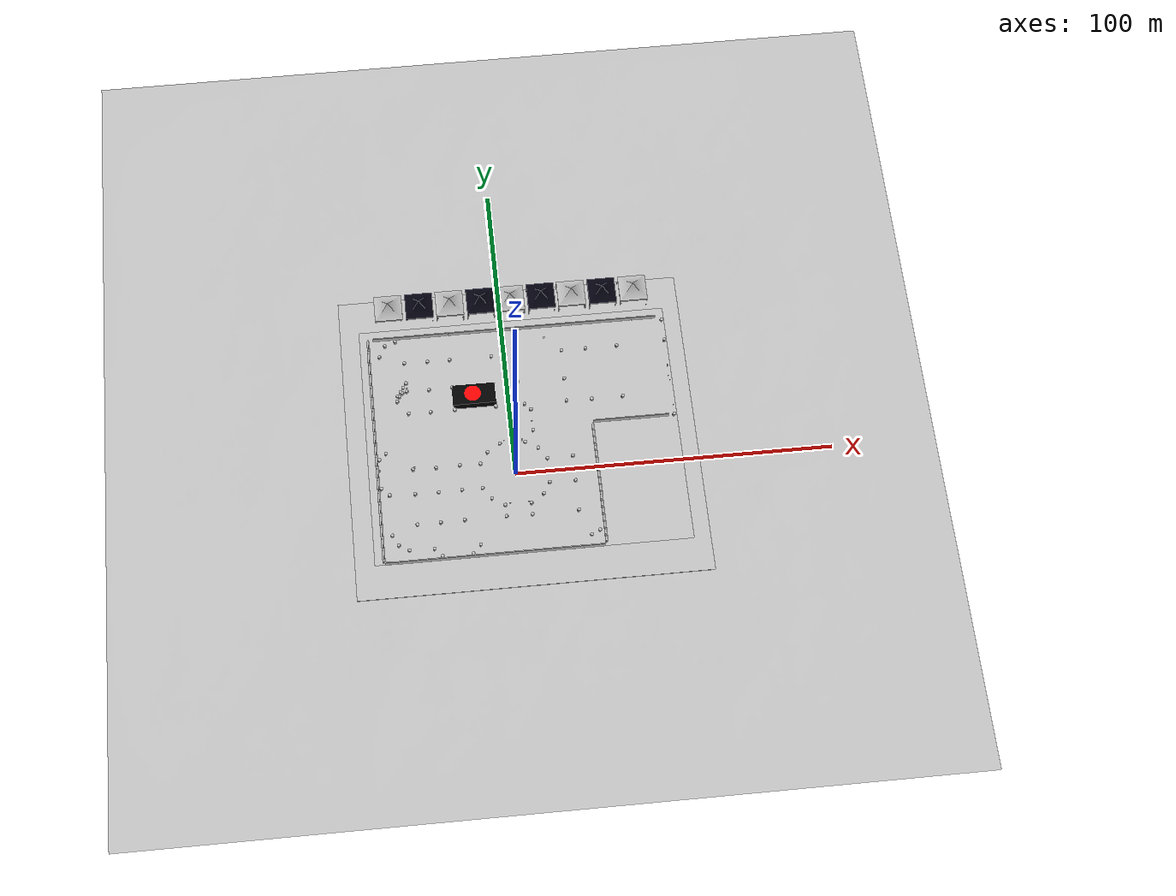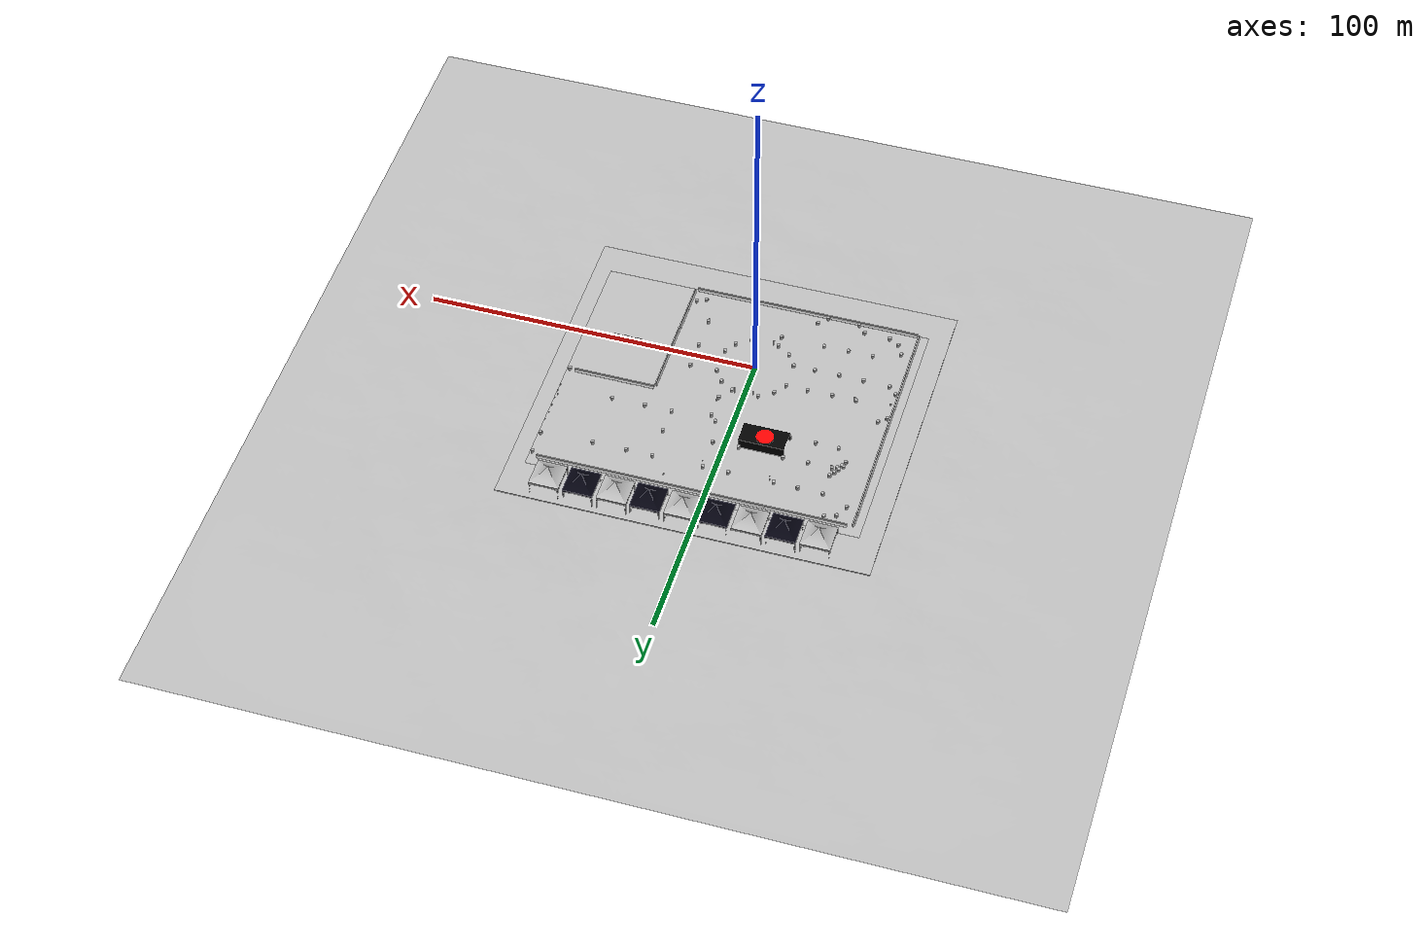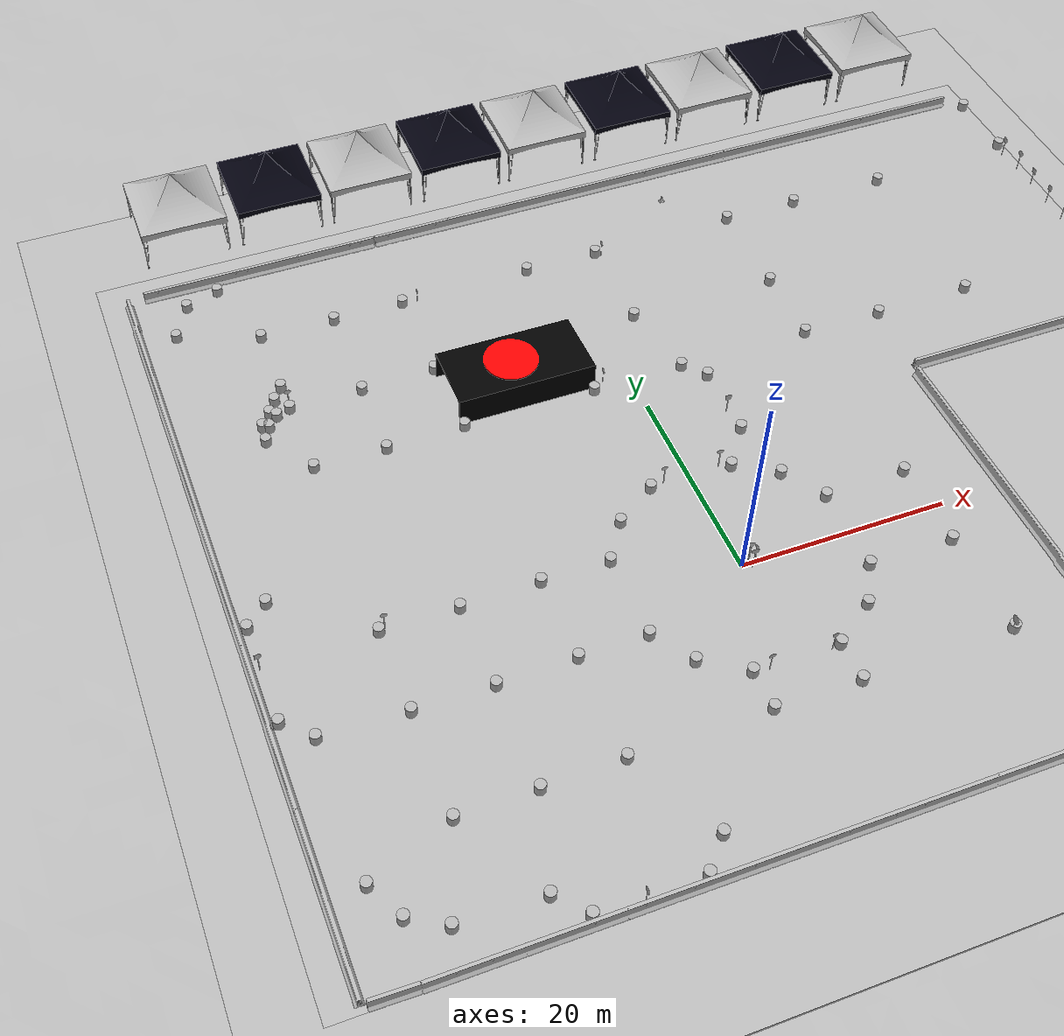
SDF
<sdf version="1.7">
 <world name="serit">
  <scene>
   <grid>false</grid>
   <ambient>0.4 0.4 0.4 1</ambient>
   <background>0.26 0.40 1.0 1</background>
   <shadows>0</shadows>
  </scene>
  <plugin filename="ignition-gazebo-physics-system" name="gz::sim::systems::Physics"/>
  <plugin filename="ignition-gazebo-user-commands-system" name="gz::sim::systems::UserCommands"/>
  <plugin filename="ignition-gazebo-scene-broadcaster-system" name="gz::sim::systems::SceneBroadcaster"/>
  <plugin filename="ignition-gazebo-contact-system" name="gz::sim::systems::Contact"/>
  <plugin filename="ignition-gazebo-sensors-system" name="ignition::gazebo::systems::Sensors">
   <render_engine>ogre2</render_engine>
  </plugin>
  <light type="directional" name="sun">
   <pose>0 0 10 0 0 0</pose>
   <diffuse>0.8 0.8 0.8 1</diffuse>
   <specular>0.2 0.2 0.2 1</specular>
   <attenuation>
    <range>1000</range>
    <constant>0.9</constant>
    <linear>0.01</linear>
    <quadratic>0.001</quadratic>
   </attenuation>
   <direction>-0.5 0.1 -0.9</direction>
  </light>
  <model name="SONPIST">
   <static>true</static>
   <link name="link">
    <collision name="collision"><geometry><mesh><uri>SONPIST.dae</uri></mesh></geometry></collision>
    <visual name="visual"><geometry><mesh><uri>SONPIST.dae</uri></mesh></geometry></visual>
   </link>
  </model>
  <model name="dur">
   <static>true</static>
   <pose>18.1686 -14.2362 0 0 0 -1.6456</pose>
   <link name="link4">
    <visual name="visual">
     <geometry><mesh><uri>model://tabelalar/meshes/dur.dae</uri><scale>1 1 1</scale></mesh></geometry>
    </visual>
   </link>
  </model>
  <model name="durak">
   <static>true</static>
   <pose>-42.1911 4.2702 0 0 0 -3.0219</pose>
   <link name="link3">
    <visual name="visual">
     <geometry><mesh><uri>model://tabelalar/meshes/durak.dae</uri><scale>1 1 1</scale></mesh></geometry>
    </visual>
   </link>
  </model>
  <model name="durak_2">
   <static>true</static>
   <pose>-20.6075 -25.5451 0 0 0 -1.5094</pose>
   <link name="link3">
    <visual name="visual">
     <geometry><mesh><uri>model://tabelalar/meshes/durak.dae</uri><scale>1 1 1</scale></mesh></geometry>
    </visual>
   </link>
  </model>
  <model name="durak_3">
   <static>true</static>
   <pose>6.7255 16.9317 0 0 0 0</pose>
   <link name="link3">
    <visual name="visual">
     <geometry><mesh><uri>model://tabelalar/meshes/durak.dae</uri><scale>1 1 1</scale></mesh></geometry>
    </visual>
   </link>
  </model>
  <model name="engelli_park">
   <static>true</static>
   <pose>52.0752 23.6383 0 0 0 -1.6550</pose>
   <link name="link5">
    <visual name="visual">
     <geometry><mesh><uri>model://tabelalar/meshes/engellipark.dae</uri><scale>1 1 1</scale></mesh></geometry>
    </visual>
   </link>
  </model>
  <model name="engelli_park2">
   <static>true</static>
   <pose>51.9513 32.1565 0 0 0 -1.5577</pose>
   <link name="link29">
    <visual name="visual">
     <geometry><mesh><uri>model://tabelalar/meshes/engellipark.dae</uri><scale>1 1 1</scale></mesh></geometry>
    </visual>
   </link>
  </model>
  <model name="engelli_park3">
   <static>true</static>
   <pose>51.9605 35.1834 0 0 0 -1.5577</pose>
   <link name="link30">
    <visual name="visual">
     <geometry><mesh><uri>model://tabelalar/meshes/engellipark.dae</uri><scale>1 1 1</scale></mesh></geometry>
    </visual>
   </link>
  </model>
  <model name="engelli_park4">
   <static>true</static>
   <pose>51.9406 40.7256 0 0 0 -1.5577</pose>
   <link name="link32">
    <visual name="visual">
     <geometry><mesh><uri>model://tabelalar/meshes/engellipark.dae</uri><scale>1 1 1</scale></mesh></geometry>
    </visual>
   </link>
  </model>
  <model name="girilmez">
   <static>true</static>
   <pose>-31.8019 31.8937 0 0 0 3.1256</pose>
   <link name="link6">
    <visual name="visual">
     <geometry><mesh><uri>/model://tabelalar/meshes/girilmez.dae</uri><scale>1 1 1</scale></mesh></geometry>
    </visual>
   </link>
  </model>
  <model name="iki_yon">
   <static>true</static>
   <pose>37 0 0 0 0 0</pose>
   <link name="link7">
    <visual name="visual">
     <geometry><mesh><uri>model://tabelalar/meshes/ikiyon.dae</uri><scale>1 1 1</scale></mesh></geometry>
    </visual>
   </link>
  </model>
  <model name="ileri">
   <static>true</static>
   <pose>-2.9745 24.0334 0 0 0 1.5017</pose>
   <link name="link8">
    <visual name="visual">
     <geometry><mesh><uri>model://tabelalar/meshes/ileri.dae</uri><scale>1 1 1</scale></mesh></geometry>
    </visual>
   </link>
  </model>
  <model name="ileri_sag">
   <static>true</static>
   <pose>36 0 0 0 0 0</pose>
   <link name="link9">
    <visual name="visual">
     <geometry><mesh><uri>model://tabelalar/meshes/ilerisag.dae</uri><scale>1 1 1</scale></mesh></geometry>
    </visual>
   </link>
  </model>
  <model name="ileri_sol">
   <static>true</static>
   <pose>-16.0518 40.5145 0 0 0 1.5295</pose>
   <link name="link10">
    <visual name="visual">
     <geometry><mesh><uri>model://tabelalar/meshes/ilerisol.dae</uri><scale>1 1 1</scale></mesh></geometry>
    </visual>
   </link>
  </model>
  <model name="kavsak">
   <static>true</static>
   <pose>3.1906 -10.4292 0 0 0 0</pose>
   <link name="link11">
    <visual name="visual">
     <geometry><mesh><uri>model://tabelalar/meshes/kavsak.dae</uri><scale>1 1 1</scale></mesh></geometry>
    </visual>
   </link>
  </model>
  <model name="kavsak_2">
   <static>true</static>
   <pose>-2.6605 -10.4292 0 0 0 0</pose>
   <link name="link35">
    <visual name="visual">
     <geometry><mesh><uri>model://tabelalar/meshes/kavsak.dae</uri><scale>1 1 1</scale></mesh></geometry>
    </visual>
   </link>
  </model>
  <model name="kavsak_3">
   <static>true</static>
   <pose>3.0269 10.9777 0 0 0 3.0479</pose>
   <link name="link39">
    <visual name="visual">
     <geometry><mesh><uri>model://tabelalar/meshes/kavsak.dae</uri><scale>1 1 1</scale></mesh></geometry>
    </visual>
   </link>
  </model>
  <model name="kavsak_4">
   <static>true</static>
   <pose>-2.5151 10.9308 0 0 0 -3.1357</pose>
   <link name="link40">
    <visual name="visual">
     <geometry><mesh><uri>model://tabelalar/meshes/kavsak.dae</uri><scale>1 1 1</scale></mesh></geometry>
    </visual>
   </link>
  </model>
  <model name="park">
   <static>true</static>
   <pose>52.0229 20.9028 0 0 0 -1.6336</pose>
   <link name="link12">
    <visual name="visual">
     <geometry><mesh><uri>model://tabelalar/meshes/park.dae</uri><scale>1 1 1</scale></mesh></geometry>
    </visual>
   </link>
  </model>
  <model name="park_yapilmaz">
   <static>true</static>
   <pose>52.0231 18.1399 0 0 0 -1.5211</pose>
   <link name="link13">
    <visual name="visual">
     <geometry><mesh><uri>model://tabelalar/meshes/parkyapilmaz.dae</uri><scale>1 1 1</scale></mesh></geometry>
    </visual>
   </link>
  </model>
  <model name="park_yapilmaz2">
   <static>true</static>
   <pose>52.0674 26.6380 0 0 0 -1.5211</pose>
   <link name="link25">
    <visual name="visual">
     <geometry><mesh><uri>model://tabelalar/meshes/parkyapilmaz.dae</uri><scale>1 1 1</scale></mesh></geometry>
    </visual>
   </link>
  </model>
  <model name="park_yapilmaz3">
   <static>true</static>
   <pose>51.9760 29.3446 0 0 0 -1.5211</pose>
   <link name="link26">
    <visual name="visual">
     <geometry><mesh><uri>model://tabelalar/meshes/parkyapilmaz.dae</uri><scale>1 1 1</scale></mesh></geometry>
    </visual>
   </link>
  </model>
  <model name="park_yapilmaz4">
   <static>true</static>
   <pose>52.0077 37.9012 0 0 0 -1.5211</pose>
   <link name="link31">
    <visual name="visual">
     <geometry><mesh><uri>model://tabelalar/meshes/parkyapilmaz.dae</uri><scale>1 1 1</scale></mesh></geometry>
    </visual>
   </link>
  </model>
  <model name="park_yasak">
   <static>true</static>
   <pose>38 0 0 0 0 0</pose>
   <link name="link14">
    <visual name="visual">
     <geometry><mesh><uri>model://tabelalar/meshes/parkyasak.dae</uri><scale>1 1 1</scale></mesh></geometry>
    </visual>
   </link>
  </model>
  <model name="saga_donus">
   <static>true</static>
   <pose>39 0 0 0 0 0</pose>
   <link name="link15">
    <visual name="visual">
     <geometry><mesh><uri>model://tabelalar/meshes/sagdonusyasak.dae</uri><scale>1 1 1</scale></mesh></geometry>
    </visual>
   </link>
  </model>
  <model name="sag_yon">
   <static>true</static>
   <pose>40 0 0 0 0 0</pose>
   <link name="link16">
    <visual name="visual">
     <geometry><mesh><uri>model://tabelalar/meshes/sagyon.dae</uri><scale>1 1 1</scale></mesh></geometry>
    </visual>
   </link>
  </model>
  <model name="sola_donus">
   <static>true</static>
   <pose>41 0 0 0 0 0</pose>
   <link name="link17">
    <visual name="visual">
     <geometry><mesh><uri>model://tabelalar/meshes/soladonus.dae</uri><scale>1 1 1</scale></mesh></geometry>
    </visual>
   </link>
  </model>
  <model name="sola_donus_yasak">
   <static>true</static>
   <pose>3.9118 40.5735 0 0 0 1.5295</pose>
   <link name="link18">
    <visual name="visual">
     <geometry><mesh><uri>model://tabelalar/meshes/soldonusyasak.dae</uri><scale>1 1 1</scale></mesh></geometry>
    </visual>
   </link>
  </model>
  <model name="sola_donus_yasak2">
   <static>true</static>
   <pose>35 0 0 0 0 0</pose>
   <link name="link33">
    <visual name="visual">
     <geometry><mesh><uri>model://tabelalar/meshes/soldonusyasak.dae</uri><scale>1 1 1</scale></mesh></geometry>
    </visual>
   </link>
  </model>
  <model name="sola_donus_yasak3">
   <static>true</static>
   <pose>-31.2415 4.4956 0 0 0 3.1232</pose>
   <link name="link34">
    <visual name="visual">
     <geometry><mesh><uri>model://tabelalar/meshes/soldonusyasak.dae</uri><scale>1 1 1</scale></mesh></geometry>
    </visual>
   </link>
  </model>
  <model name="sol_sag">
   <static>true</static>
   <pose>42 0 0 0 0 0</pose>
   <link name="link19">
    <visual name="visual">
     <geometry><mesh><uri>model://tabelalar/meshes/solsag.dae</uri><scale>1 1 1</scale></mesh></geometry>
    </visual>
   </link>
  </model>
  <model name="sol_yon">
   <static>true</static>
   <pose>0.8754 -0.3927 0 0 0 -0.0827</pose>
   <link name="link20">
    <visual name="visual">
     <geometry><mesh><uri>model://tabelalar/meshes/solyon.dae</uri><scale>1 1 1</scale></mesh></geometry>
    </visual>
   </link>
  </model>
  <model name="sol_yon2">
   <static>true</static>
   <pose>1.1308 -0.0790 0 0 0 1.5742</pose>
   <link name="link36">
    <visual name="visual">
     <geometry><mesh><uri>model://tabelalar/meshes/solyon.dae</uri><scale>1 1 1</scale></mesh></geometry>
    </visual>
   </link>
  </model>
  <model name="sol_yon3">
   <static>true</static>
   <pose>0.4828 -0.0661 0 0 0 -1.6431</pose>
   <link name="link37">
    <visual name="visual">
     <geometry><mesh><uri>model://tabelalar/meshes/solyon.dae</uri><scale>1 1 1</scale></mesh></geometry>
    </visual>
   </link>
  </model>
  <model name="sol_yon4">
   <static>true</static>
   <pose>0.7949 0.3440 0 0 0 3.0904</pose>
   <link name="link38">
    <visual name="visual">
     <geometry><mesh><uri>model://tabelalar/meshes/solyon.dae</uri><scale>1 1 1</scale></mesh></geometry>
    </visual>
   </link>
  </model>
  <model name="trafige_kapali">
   <static>true</static>
   <pose>43 0 0 0 0 0</pose>
   <link name="link21">
    <visual name="visual">
     <geometry><mesh><uri>model://tabelalar/meshes/trafigekapali.dae</uri><scale>1 1 1</scale></mesh></geometry>
    </visual>
   </link>
  </model>
  <model name="koni">
   <static>true</static>
   <pose>13.6057 46.748 0 0 0 0</pose>
   <link name="link22">
    <visual name="visual">
     <geometry><mesh><uri>model://dekorasyon/koni/koni.dae</uri><scale>1 1 1</scale></mesh></geometry>
    </visual>
   </link>
  </model>
  <model name="bariyerTamamlanmış">
   <static>true</static>
   <pose>-0.4989 0.4262 0 0 0 0</pose>
   <link name="link24">
    <visual name="visual">
     <geometry><mesh><uri>model://dekorasyon/engel2/engel.dae</uri><scale>1 1 1</scale></mesh></geometry>
    </visual>
   </link>
  </model>
  <model name="asfalt">
   <static>true</static>
   <link name="link24">
    <visual name="visual">
     <geometry>
      <mesh><uri>model://silme kendi modellerin/asfalt/asfalt.dae</uri><scale>1 1 1</scale></mesh>
     </geometry>
    </visual>
   </link>
  </model>
  <model name="çadır">
   <static>true</static>
   <link name="link24">
    <visual name="visual">
     <geometry><mesh><uri>model://silme kendi modellerin/cadir/tent.dae</uri><scale>1 1 1</scale></mesh></geometry>
    </visual>
   </link>
  </model>
  <model name="dene">
   <static>true</static>
   <pose>-0 0 -0.5486 0 0 0</pose>
   <link name="link24">
    <visual name="visual">
     <geometry><mesh><uri>model://silme kendi modellerin/patch.dae</uri><scale>2 2 2</scale></mesh></geometry>
    </visual>
   </link>
  </model>
  <model name="cylinder">
   <pose>18.6879 41.3851 0.499999 0 -0 0</pose>
   <link name="cylinder_link">
    <inertial>
     <inertia>
      <ixx>0.14580000000000001</ixx>
      <ixy>0</ixy>
      <ixz>0</ixz>
      <iyy>0.14580000000000001</iyy>
      <iyz>0</iyz>
      <izz>0.125</izz>
     </inertia>
     <mass>1</mass>
    </inertial>
    <collision name="cylinder_collision">
     <geometry><cylinder><radius>0.5</radius><length>1</length></cylinder></geometry>
    </collision>
    <visual name="cylinder_visual">
     <geometry><cylinder><radius>0.5</radius><length>1</length></cylinder></geometry>
     <material>
      <ambient>0.3 0.3 0.3 1</ambient>
      <diffuse>0.7 0.7 0.7 1</diffuse>
      <specular>1 1 1 1</specular>
     </material>
    </visual>
   </link>
   <static>false</static>
  </model>
  <model name="cylinder_0">
   <pose>18.5999 31.3107 0.499999 -0 0 0</pose>
   <link name="cylinder_link">
    <inertial>
     <inertia>
      <ixx>0.14580000000000001</ixx>
      <ixy>0</ixy>
      <ixz>0</ixz>
      <iyy>0.14580000000000001</iyy>
      <iyz>0</iyz>
      <izz>0.125</izz>
     </inertia>
     <mass>1</mass>
    </inertial>
    <collision name="cylinder_collision">
     <geometry><cylinder><radius>0.5</radius><length>1</length></cylinder></geometry>
    </collision>
    <visual name="cylinder_visual">
     <geometry><cylinder><radius>0.5</radius><length>1</length></cylinder></geometry>
     <material>
      <ambient>0.3 0.3 0.3 1</ambient>
      <diffuse>0.7 0.7 0.7 1</diffuse>
      <specular>1 1 1 1</specular>
     </material>
    </visual>
   </link>
   <static>false</static>
  </model>
  <model name="cylinder_1">
   <pose>3.60432 31.5038 0.499999 0 0 0</pose>
   <link name="cylinder_link">
    <inertial>
     <inertia>
      <ixx>0.14580000000000001</ixx>
      <ixy>0</ixy>
      <ixz>0</ixz>
      <iyy>0.14580000000000001</iyy>
      <iyz>0</iyz>
      <izz>0.125</izz>
     </inertia>
     <mass>1</mass>
    </inertial>
    <collision name="cylinder_collision">
     <geometry><cylinder><radius>0.5</radius><length>1</length></cylinder></geometry>
    </collision>
    <visual name="cylinder_visual">
     <geometry><cylinder><radius>0.5</radius><length>1</length></cylinder></geometry>
     <material>
      <ambient>0.3 0.3 0.3 1</ambient>
      <diffuse>0.7 0.7 0.7 1</diffuse>
      <specular>1 1 1 1</specular>
     </material>
    </visual>
   </link>
   <static>false</static>
  </model>
  <model name="cylinder_2">
   <pose>3.5888 41.3303 0.499999 0 0 -0</pose>
   <link name="cylinder_link">
    <inertial>
     <inertia>
      <ixx>0.14580000000000001</ixx>
      <ixy>0</ixy>
      <ixz>0</ixz>
      <iyy>0.14580000000000001</iyy>
      <iyz>0</iyz>
      <izz>0.125</izz>
     </inertia>
     <mass>1</mass>
    </inertial>
    <collision name="cylinder_collision">
     <geometry><cylinder><radius>0.5</radius><length>1</length></cylinder></geometry>
    </collision>
    <visual name="cylinder_visual">
     <geometry><cylinder><radius>0.5</radius><length>1</length></cylinder></geometry>
     <material>
      <ambient>0.3 0.3 0.3 1</ambient>
      <diffuse>0.7 0.7 0.7 1</diffuse>
      <specular>1 1 1 1</specular>
     </material>
    </visual>
   </link>
   <static>false</static>
  </model>
  <model name="cylinder_3">
   <pose>-3.96703 41.3411 0.499999 -0 0 0</pose>
   <link name="cylinder_link">
    <inertial>
     <inertia>
      <ixx>0.14580000000000001</ixx>
      <ixy>0</ixy>
      <ixz>0</ixz>
      <iyy>0.14580000000000001</iyy>
      <iyz>0</iyz>
      <izz>0.125</izz>
     </inertia>
     <mass>1</mass>
    </inertial>
    <collision name="cylinder_collision">
     <geometry><cylinder><radius>0.5</radius><length>1</length></cylinder></geometry>
    </collision>
    <visual name="cylinder_visual">
     <geometry><cylinder><radius>0.5</radius><length>1</length></cylinder></geometry>
     <material>
      <ambient>0.3 0.3 0.3 1</ambient>
      <diffuse>0.7 0.7 0.7 1</diffuse>
      <specular>1 1 1 1</specular>
     </material>
    </visual>
   </link>
   <static>false</static>
  </model>
  <model name="cylinder_4">
   <pose>-4.07755 31.3093 0.499999 0 0 0</pose>
   <link name="cylinder_link">
    <inertial>
     <inertia>
      <ixx>0.14580000000000001</ixx>
      <ixy>0</ixy>
      <ixz>0</ixz>
      <iyy>0.14580000000000001</iyy>
      <iyz>0</iyz>
      <izz>0.125</izz>
     </inertia>
     <mass>1</mass>
    </inertial>
    <collision name="cylinder_collision">
     <geometry><cylinder><radius>0.5</radius><length>1</length></cylinder></geometry>
    </collision>
    <visual name="cylinder_visual">
     <geometry><cylinder><radius>0.5</radius><length>1</length></cylinder></geometry>
     <material>
      <ambient>0.3 0.3 0.3 1</ambient>
      <diffuse>0.7 0.7 0.7 1</diffuse>
      <specular>1 1 1 1</specular>
     </material>
    </visual>
   </link>
   <static>false</static>
  </model>
  <model name="cylinder_5">
   <pose>-17.3787 41.2742 0.499999 0 0 0</pose>
   <link name="cylinder_link">
    <inertial>
     <inertia>
      <ixx>0.14580000000000001</ixx>
      <ixy>0</ixy>
      <ixz>0</ixz>
      <iyy>0.14580000000000001</iyy>
      <iyz>0</iyz>
      <izz>0.125</izz>
     </inertia>
     <mass>1</mass>
    </inertial>
    <collision name="cylinder_collision">
     <geometry><cylinder><radius>0.5</radius><length>1</length></cylinder></geometry>
    </collision>
    <visual name="cylinder_visual">
     <geometry><cylinder><radius>0.5</radius><length>1</length></cylinder></geometry>
     <material>
      <ambient>0.3 0.3 0.3 1</ambient>
      <diffuse>0.7 0.7 0.7 1</diffuse>
      <specular>1 1 1 1</specular>
     </material>
    </visual>
   </link>
   <static>false</static>
  </model>
  <model name="cylinder_6">
   <pose>-17.3886 31.5031 0.499999 -0 0 0</pose>
   <link name="cylinder_link">
    <inertial>
     <inertia>
      <ixx>0.14580000000000001</ixx>
      <ixy>0</ixy>
      <ixz>0</ixz>
      <iyy>0.14580000000000001</iyy>
      <iyz>0</iyz>
      <izz>0.125</izz>
     </inertia>
     <mass>1</mass>
    </inertial>
    <collision name="cylinder_collision">
     <geometry><cylinder><radius>0.5</radius><length>1</length></cylinder></geometry>
    </collision>
    <visual name="cylinder_visual">
     <geometry><cylinder><radius>0.5</radius><length>1</length></cylinder></geometry>
     <material>
      <ambient>0.3 0.3 0.3 1</ambient>
      <diffuse>0.7 0.7 0.7 1</diffuse>
      <specular>1 1 1 1</specular>
     </material>
    </visual>
   </link>
   <static>false</static>
  </model>
  <model name="cylinder_7">
   <pose>-24.4995 41.3196 0.499999 0 0 -0</pose>
   <link name="cylinder_link">
    <inertial>
     <inertia>
      <ixx>0.14580000000000001</ixx>
      <ixy>0</ixy>
      <ixz>0</ixz>
      <iyy>0.14580000000000001</iyy>
      <iyz>0</iyz>
      <izz>0.125</izz>
     </inertia>
     <mass>1</mass>
    </inertial>
    <collision name="cylinder_collision">
     <geometry><cylinder><radius>0.5</radius><length>1</length></cylinder></geometry>
    </collision>
    <visual name="cylinder_visual">
     <geometry><cylinder><radius>0.5</radius><length>1</length></cylinder></geometry>
     <material>
      <ambient>0.3 0.3 0.3 1</ambient>
      <diffuse>0.7 0.7 0.7 1</diffuse>
      <specular>1 1 1 1</specular>
     </material>
    </visual>
   </link>
   <static>false</static>
  </model>
  <model name="cylinder_8">
   <pose>-31.9164 41.4634 0.499999 -0 0 0</pose>
   <link name="cylinder_link">
    <inertial>
     <inertia>
      <ixx>0.14580000000000001</ixx>
      <ixy>0</ixy>
      <ixz>0</ixz>
      <iyy>0.14580000000000001</iyy>
      <iyz>0</iyz>
      <izz>0.125</izz>
     </inertia>
     <mass>1</mass>
    </inertial>
    <collision name="cylinder_collision">
     <geometry><cylinder><radius>0.5</radius><length>1</length></cylinder></geometry>
    </collision>
    <visual name="cylinder_visual">
     <geometry><cylinder><radius>0.5</radius><length>1</length></cylinder></geometry>
     <material>
      <ambient>0.3 0.3 0.3 1</ambient>
      <diffuse>0.7 0.7 0.7 1</diffuse>
      <specular>1 1 1 1</specular>
     </material>
    </visual>
   </link>
   <static>false</static>
  </model>
  <model name="cylinder_9">
   <pose>-31.8709 31.4062 0.499999 0 -0 0</pose>
   <link name="cylinder_link">
    <inertial>
     <inertia>
      <ixx>0.14580000000000001</ixx>
      <ixy>0</ixy>
      <ixz>0</ixz>
      <iyy>0.14580000000000001</iyy>
      <iyz>0</iyz>
      <izz>0.125</izz>
     </inertia>
     <mass>1</mass>
    </inertial>
    <collision name="cylinder_collision">
     <geometry><cylinder><radius>0.5</radius><length>1</length></cylinder></geometry>
    </collision>
    <visual name="cylinder_visual">
     <geometry><cylinder><radius>0.5</radius><length>1</length></cylinder></geometry>
     <material>
      <ambient>0.3 0.3 0.3 1</ambient>
      <diffuse>0.7 0.7 0.7 1</diffuse>
      <specular>1 1 1 1</specular>
     </material>
    </visual>
   </link>
   <static>false</static>
  </model>
  <model name="cylinder_10">
   <pose>-24.754 31.3505 0.499999 -0 -0 -0</pose>
   <link name="cylinder_link">
    <inertial>
     <inertia>
      <ixx>0.14580000000000001</ixx>
      <ixy>0</ixy>
      <ixz>0</ixz>
      <iyy>0.14580000000000001</iyy>
      <iyz>0</iyz>
      <izz>0.125</izz>
     </inertia>
     <mass>1</mass>
    </inertial>
    <collision name="cylinder_collision">
     <geometry><cylinder><radius>0.5</radius><length>1</length></cylinder></geometry>
    </collision>
    <visual name="cylinder_visual">
     <geometry><cylinder><radius>0.5</radius><length>1</length></cylinder></geometry>
     <material>
      <ambient>0.3 0.3 0.3 1</ambient>
      <diffuse>0.7 0.7 0.7 1</diffuse>
      <specular>1 1 1 1</specular>
     </material>
    </visual>
   </link>
   <static>false</static>
  </model>
  <model name="cylinder_11">
   <pose>-31.8078 23.6026 0.499999 -0 0 0</pose>
   <link name="cylinder_link">
    <inertial>
     <inertia>
      <ixx>0.14580000000000001</ixx>
      <ixy>0</ixy>
      <ixz>0</ixz>
      <iyy>0.14580000000000001</iyy>
      <iyz>0</iyz>
      <izz>0.125</izz>
     </inertia>
     <mass>1</mass>
    </inertial>
    <collision name="cylinder_collision">
     <geometry><cylinder><radius>0.5</radius><length>1</length></cylinder></geometry>
    </collision>
    <visual name="cylinder_visual">
     <geometry><cylinder><radius>0.5</radius><length>1</length></cylinder></geometry>
     <material>
      <ambient>0.3 0.3 0.3 1</ambient>
      <diffuse>0.7 0.7 0.7 1</diffuse>
      <specular>1 1 1 1</specular>
     </material>
    </visual>
   </link>
   <static>false</static>
  </model>
  <model name="cylinder_12">
   <pose>-31.8202 4.32407 0.499999 0 0 0</pose>
   <link name="cylinder_link">
    <inertial>
     <inertia>
      <ixx>0.14580000000000001</ixx>
      <ixy>0</ixy>
      <ixz>0</ixz>
      <iyy>0.14580000000000001</iyy>
      <iyz>0</iyz>
      <izz>0.125</izz>
     </inertia>
     <mass>1</mass>
    </inertial>
    <collision name="cylinder_collision">
     <geometry><cylinder><radius>0.5</radius><length>1</length></cylinder></geometry>
    </collision>
    <visual name="cylinder_visual">
     <geometry><cylinder><radius>0.5</radius><length>1</length></cylinder></geometry>
     <material>
      <ambient>0.3 0.3 0.3 1</ambient>
      <diffuse>0.7 0.7 0.7 1</diffuse>
      <specular>1 1 1 1</specular>
     </material>
    </visual>
   </link>
   <static>false</static>
  </model>
  <model name="cylinder_13">
   <pose>-24.5894 4.23341 0.499999 -0 0 -0</pose>
   <link name="cylinder_link">
    <inertial>
     <inertia>
      <ixx>0.14580000000000001</ixx>
      <ixy>0</ixy>
      <ixz>0</ixz>
      <iyy>0.14580000000000001</iyy>
      <iyz>0</iyz>
      <izz>0.125</izz>
     </inertia>
     <mass>1</mass>
    </inertial>
    <collision name="cylinder_collision">
     <geometry><cylinder><radius>0.5</radius><length>1</length></cylinder></geometry>
    </collision>
    <visual name="cylinder_visual">
     <geometry><cylinder><radius>0.5</radius><length>1</length></cylinder></geometry>
     <material>
      <ambient>0.3 0.3 0.3 1</ambient>
      <diffuse>0.7 0.7 0.7 1</diffuse>
      <specular>1 1 1 1</specular>
     </material>
    </visual>
   </link>
   <static>false</static>
  </model>
  <model name="cylinder_14">
   <pose>-24.8482 23.4571 0.499999 0 0 0</pose>
   <link name="cylinder_link">
    <inertial>
     <inertia>
      <ixx>0.14580000000000001</ixx>
      <ixy>0</ixy>
      <ixz>0</ixz>
      <iyy>0.14580000000000001</iyy>
      <iyz>0</iyz>
      <izz>0.125</izz>
     </inertia>
     <mass>1</mass>
    </inertial>
    <collision name="cylinder_collision">
     <geometry><cylinder><radius>0.5</radius><length>1</length></cylinder></geometry>
    </collision>
    <visual name="cylinder_visual">
     <geometry><cylinder><radius>0.5</radius><length>1</length></cylinder></geometry>
     <material>
      <ambient>0.3 0.3 0.3 1</ambient>
      <diffuse>0.7 0.7 0.7 1</diffuse>
      <specular>1 1 1 1</specular>
     </material>
    </visual>
   </link>
   <static>false</static>
  </model>
  <model name="cylinder_15">
   <pose>-17.1251 4.36566 0.499999 -0 0 0</pose>
   <link name="cylinder_link">
    <inertial>
     <inertia>
      <ixx>0.14580000000000001</ixx>
      <ixy>0</ixy>
      <ixz>0</ixz>
      <iyy>0.14580000000000001</iyy>
      <iyz>0</iyz>
      <izz>0.125</izz>
     </inertia>
     <mass>1</mass>
    </inertial>
    <collision name="cylinder_collision">
     <geometry><cylinder><radius>0.5</radius><length>1</length></cylinder></geometry>
    </collision>
    <visual name="cylinder_visual">
     <geometry><cylinder><radius>0.5</radius><length>1</length></cylinder></geometry>
     <material>
      <ambient>0.3 0.3 0.3 1</ambient>
      <diffuse>0.7 0.7 0.7 1</diffuse>
      <specular>1 1 1 1</specular>
     </material>
    </visual>
   </link>
   <static>false</static>
  </model>
  <model name="cylinder_16">
   <pose>-10.6307 4.29542 0.499999 -0 -0 0</pose>
   <link name="cylinder_link">
    <inertial>
     <inertia>
      <ixx>0.14580000000000001</ixx>
      <ixy>0</ixy>
      <ixz>0</ixz>
      <iyy>0.14580000000000001</iyy>
      <iyz>0</iyz>
      <izz>0.125</izz>
     </inertia>
     <mass>1</mass>
    </inertial>
    <collision name="cylinder_collision">
     <geometry><cylinder><radius>0.5</radius><length>1</length></cylinder></geometry>
    </collision>
    <visual name="cylinder_visual">
     <geometry><cylinder><radius>0.5</radius><length>1</length></cylinder></geometry>
     <material>
      <ambient>0.3 0.3 0.3 1</ambient>
      <diffuse>0.7 0.7 0.7 1</diffuse>
      <specular>1 1 1 1</specular>
     </material>
    </visual>
   </link>
   <static>false</static>
  </model>
  <model name="cylinder_17">
   <pose>-8.08607 7.95931 0.499999 0 0 0</pose>
   <link name="cylinder_link">
    <inertial>
     <inertia>
      <ixx>0.14580000000000001</ixx>
      <ixy>0</ixy>
      <ixz>0</ixz>
      <iyy>0.14580000000000001</iyy>
      <iyz>0</iyz>
      <izz>0.125</izz>
     </inertia>
     <mass>1</mass>
    </inertial>
    <collision name="cylinder_collision">
     <geometry><cylinder><radius>0.5</radius><length>1</length></cylinder></geometry>
    </collision>
    <visual name="cylinder_visual">
     <geometry><cylinder><radius>0.5</radius><length>1</length></cylinder></geometry>
     <material>
      <ambient>0.3 0.3 0.3 1</ambient>
      <diffuse>0.7 0.7 0.7 1</diffuse>
      <specular>1 1 1 1</specular>
     </material>
    </visual>
   </link>
   <static>false</static>
  </model>
  <model name="cylinder_18">
   <pose>-3.95242 10.6224 0.499999 0 0 0</pose>
   <link name="cylinder_link">
    <inertial>
     <inertia>
      <ixx>0.14580000000000001</ixx>
      <ixy>0</ixy>
      <ixz>0</ixz>
      <iyy>0.14580000000000001</iyy>
      <iyz>0</iyz>
      <izz>0.125</izz>
     </inertia>
     <mass>1</mass>
    </inertial>
    <collision name="cylinder_collision">
     <geometry><cylinder><radius>0.5</radius><length>1</length></cylinder></geometry>
    </collision>
    <visual name="cylinder_visual">
     <geometry><cylinder><radius>0.5</radius><length>1</length></cylinder></geometry>
     <material>
      <ambient>0.3 0.3 0.3 1</ambient>
      <diffuse>0.7 0.7 0.7 1</diffuse>
      <specular>1 1 1 1</specular>
     </material>
    </visual>
   </link>
   <static>false</static>
  </model>
  <model name="cylinder_19">
   <pose>-4.0011 23.5643 0.499999 0 -0 -0</pose>
   <link name="cylinder_link">
    <inertial>
     <inertia>
      <ixx>0.14580000000000001</ixx>
      <ixy>0</ixy>
      <ixz>0</ixz>
      <iyy>0.14580000000000001</iyy>
      <iyz>0</iyz>
      <izz>0.125</izz>
     </inertia>
     <mass>1</mass>
    </inertial>
    <collision name="cylinder_collision">
     <geometry><cylinder><radius>0.5</radius><length>1</length></cylinder></geometry>
    </collision>
    <visual name="cylinder_visual">
     <geometry><cylinder><radius>0.5</radius><length>1</length></cylinder></geometry>
     <material>
      <ambient>0.3 0.3 0.3 1</ambient>
      <diffuse>0.7 0.7 0.7 1</diffuse>
      <specular>1 1 1 1</specular>
     </material>
    </visual>
   </link>
   <static>false</static>
  </model>
  <model name="cylinder_20">
   <pose>-17.1509 23.587 0.499999 -0 0 0</pose>
   <link name="cylinder_link">
    <inertial>
     <inertia>
      <ixx>0.14580000000000001</ixx>
      <ixy>0</ixy>
      <ixz>0</ixz>
      <iyy>0.14580000000000001</iyy>
      <iyz>0</iyz>
      <izz>0.125</izz>
     </inertia>
     <mass>1</mass>
    </inertial>
    <collision name="cylinder_collision">
     <geometry><cylinder><radius>0.5</radius><length>1</length></cylinder></geometry>
    </collision>
    <visual name="cylinder_visual">
     <geometry><cylinder><radius>0.5</radius><length>1</length></cylinder></geometry>
     <material>
      <ambient>0.3 0.3 0.3 1</ambient>
      <diffuse>0.7 0.7 0.7 1</diffuse>
      <specular>1 1 1 1</specular>
     </material>
    </visual>
   </link>
   <static>false</static>
  </model>
  <model name="cylinder_21">
   <pose>6.92482 21.5291 0.499999 -0 -0 0</pose>
   <link name="cylinder_link">
    <inertial>
     <inertia>
      <ixx>0.14580000000000001</ixx>
      <ixy>0</ixy>
      <ixz>0</ixz>
      <iyy>0.14580000000000001</iyy>
      <iyz>0</iyz>
      <izz>0.125</izz>
     </inertia>
     <mass>1</mass>
    </inertial>
    <collision name="cylinder_collision">
     <geometry><cylinder><radius>0.5</radius><length>1</length></cylinder></geometry>
    </collision>
    <visual name="cylinder_visual">
     <geometry><cylinder><radius>0.5</radius><length>1</length></cylinder></geometry>
     <material>
      <ambient>0.3 0.3 0.3 1</ambient>
      <diffuse>0.7 0.7 0.7 1</diffuse>
      <specular>1 1 1 1</specular>
     </material>
    </visual>
   </link>
   <static>false</static>
  </model>
  <model name="cylinder_22">
   <pose>6.91347 14.2952 0.499999 0 -0 0</pose>
   <link name="cylinder_link">
    <inertial>
     <inertia>
      <ixx>0.14580000000000001</ixx>
      <ixy>0</ixy>
      <ixz>0</ixz>
      <iyy>0.14580000000000001</iyy>
      <iyz>0</iyz>
      <izz>0.125</izz>
     </inertia>
     <mass>1</mass>
    </inertial>
    <collision name="cylinder_collision">
     <geometry><cylinder><radius>0.5</radius><length>1</length></cylinder></geometry>
    </collision>
    <visual name="cylinder_visual">
     <geometry><cylinder><radius>0.5</radius><length>1</length></cylinder></geometry>
     <material>
      <ambient>0.3 0.3 0.3 1</ambient>
      <diffuse>0.7 0.7 0.7 1</diffuse>
      <specular>1 1 1 1</specular>
     </material>
    </visual>
   </link>
   <static>false</static>
  </model>
  <model name="cylinder_23">
   <pose>4.03038 10.464 0.499999 -0 -0 -0</pose>
   <link name="cylinder_link">
    <inertial>
     <inertia>
      <ixx>0.14580000000000001</ixx>
      <ixy>0</ixy>
      <ixz>0</ixz>
      <iyy>0.14580000000000001</iyy>
      <iyz>0</iyz>
      <izz>0.125</izz>
     </inertia>
     <mass>1</mass>
    </inertial>
    <collision name="cylinder_collision">
     <geometry><cylinder><radius>0.5</radius><length>1</length></cylinder></geometry>
    </collision>
    <visual name="cylinder_visual">
     <geometry><cylinder><radius>0.5</radius><length>1</length></cylinder></geometry>
     <material>
      <ambient>0.3 0.3 0.3 1</ambient>
      <diffuse>0.7 0.7 0.7 1</diffuse>
      <specular>1 1 1 1</specular>
     </material>
    </visual>
   </link>
   <static>false</static>
  </model>
  <model name="cylinder_24">
   <pose>10.4649 4.22367 0.499999 -0 0 0</pose>
   <link name="cylinder_link">
    <inertial>
     <inertia>
      <ixx>0.14580000000000001</ixx>
      <ixy>0</ixy>
      <ixz>0</ixz>
      <iyy>0.14580000000000001</iyy>
      <iyz>0</iyz>
      <izz>0.125</izz>
     </inertia>
     <mass>1</mass>
    </inertial>
    <collision name="cylinder_collision">
     <geometry><cylinder><radius>0.5</radius><length>1</length></cylinder></geometry>
    </collision>
    <visual name="cylinder_visual">
     <geometry><cylinder><radius>0.5</radius><length>1</length></cylinder></geometry>
     <material>
      <ambient>0.3 0.3 0.3 1</ambient>
      <diffuse>0.7 0.7 0.7 1</diffuse>
      <specular>1 1 1 1</specular>
     </material>
    </visual>
   </link>
   <static>false</static>
  </model>
  <model name="cylinder_25">
   <pose>7.89231 8.06475 0.499999 0 -0 -0</pose>
   <link name="cylinder_link">
    <inertial>
     <inertia>
      <ixx>0.14580000000000001</ixx>
      <ixy>0</ixy>
      <ixz>0</ixz>
      <iyy>0.14580000000000001</iyy>
      <iyz>0</iyz>
      <izz>0.125</izz>
     </inertia>
     <mass>1</mass>
    </inertial>
    <collision name="cylinder_collision">
     <geometry><cylinder><radius>0.5</radius><length>1</length></cylinder></geometry>
    </collision>
    <visual name="cylinder_visual">
     <geometry><cylinder><radius>0.5</radius><length>1</length></cylinder></geometry>
     <material>
      <ambient>0.3 0.3 0.3 1</ambient>
      <diffuse>0.7 0.7 0.7 1</diffuse>
      <specular>1 1 1 1</specular>
     </material>
    </visual>
   </link>
   <static>false</static>
  </model>
  <model name="cylinder_26">
   <pose>18.5067 4.40915 0.499999 0 0 0</pose>
   <link name="cylinder_link">
    <inertial>
     <inertia>
      <ixx>0.14580000000000001</ixx>
      <ixy>0</ixy>
      <ixz>0</ixz>
      <iyy>0.14580000000000001</iyy>
      <iyz>0</iyz>
      <izz>0.125</izz>
     </inertia>
     <mass>1</mass>
    </inertial>
    <collision name="cylinder_collision">
     <geometry><cylinder><radius>0.5</radius><length>1</length></cylinder></geometry>
    </collision>
    <visual name="cylinder_visual">
     <geometry><cylinder><radius>0.5</radius><length>1</length></cylinder></geometry>
     <material>
      <ambient>0.3 0.3 0.3 1</ambient>
      <diffuse>0.7 0.7 0.7 1</diffuse>
      <specular>1 1 1 1</specular>
     </material>
    </visual>
   </link>
   <static>false</static>
  </model>
  <model name="cylinder_27">
   <pose>18.47 23.4767 0.499999 0 -0 0</pose>
   <link name="cylinder_link">
    <inertial>
     <inertia>
      <ixx>0.14580000000000001</ixx>
      <ixy>0</ixy>
      <ixz>0</ixz>
      <iyy>0.14580000000000001</iyy>
      <iyz>0</iyz>
      <izz>0.125</izz>
     </inertia>
     <mass>1</mass>
    </inertial>
    <collision name="cylinder_collision">
     <geometry><cylinder><radius>0.5</radius><length>1</length></cylinder></geometry>
    </collision>
    <visual name="cylinder_visual">
     <geometry><cylinder><radius>0.5</radius><length>1</length></cylinder></geometry>
     <material>
      <ambient>0.3 0.3 0.3 1</ambient>
      <diffuse>0.7 0.7 0.7 1</diffuse>
      <specular>1 1 1 1</specular>
     </material>
    </visual>
   </link>
   <static>false</static>
  </model>
  <model name="cylinder_28">
   <pose>5.12296 23.5822 0.499999 -0 -0 -0</pose>
   <link name="cylinder_link">
    <inertial>
     <inertia>
      <ixx>0.14580000000000001</ixx>
      <ixy>0</ixy>
      <ixz>0</ixz>
      <iyy>0.14580000000000001</iyy>
      <iyz>0</iyz>
      <izz>0.125</izz>
     </inertia>
     <mass>1</mass>
    </inertial>
    <collision name="cylinder_collision">
     <geometry><cylinder><radius>0.5</radius><length>1</length></cylinder></geometry>
    </collision>
    <visual name="cylinder_visual">
     <geometry><cylinder><radius>0.5</radius><length>1</length></cylinder></geometry>
     <material>
      <ambient>0.3 0.3 0.3 1</ambient>
      <diffuse>0.7 0.7 0.7 1</diffuse>
      <specular>1 1 1 1</specular>
     </material>
    </visual>
   </link>
   <static>false</static>
  </model>
  <model name="cylinder_29">
   <pose>10.3538 -3.92235 0.499999 -0 -0 -0</pose>
   <link name="cylinder_link">
    <inertial>
     <inertia>
      <ixx>0.14580000000000001</ixx>
      <ixy>0</ixy>
      <ixz>0</ixz>
      <iyy>0.14580000000000001</iyy>
      <iyz>0</iyz>
      <izz>0.125</izz>
     </inertia>
     <mass>1</mass>
    </inertial>
    <collision name="cylinder_collision">
     <geometry><cylinder><radius>0.5</radius><length>1</length></cylinder></geometry>
    </collision>
    <visual name="cylinder_visual">
     <geometry><cylinder><radius>0.5</radius><length>1</length></cylinder></geometry>
     <material>
      <ambient>0.3 0.3 0.3 1</ambient>
      <diffuse>0.7 0.7 0.7 1</diffuse>
      <specular>1 1 1 1</specular>
     </material>
    </visual>
   </link>
   <static>false</static>
  </model>
  <model name="cylinder_30">
   <pose>8.13568 -7.53612 0.499999 -0 -0 0</pose>
   <link name="cylinder_link">
    <inertial>
     <inertia>
      <ixx>0.14580000000000001</ixx>
      <ixy>0</ixy>
      <ixz>0</ixz>
      <iyy>0.14580000000000001</iyy>
      <iyz>0</iyz>
      <izz>0.125</izz>
     </inertia>
     <mass>1</mass>
    </inertial>
    <collision name="cylinder_collision">
     <geometry><cylinder><radius>0.5</radius><length>1</length></cylinder></geometry>
    </collision>
    <visual name="cylinder_visual">
     <geometry><cylinder><radius>0.5</radius><length>1</length></cylinder></geometry>
     <material>
      <ambient>0.3 0.3 0.3 1</ambient>
      <diffuse>0.7 0.7 0.7 1</diffuse>
      <specular>1 1 1 1</specular>
     </material>
    </visual>
   </link>
   <static>false</static>
  </model>
  <model name="cylinder_31">
   <pose>4.00866 -10.3472 0.499999 -0 -0 0</pose>
   <link name="cylinder_link">
    <inertial>
     <inertia>
      <ixx>0.14580000000000001</ixx>
      <ixy>0</ixy>
      <ixz>0</ixz>
      <iyy>0.14580000000000001</iyy>
      <iyz>0</iyz>
      <izz>0.125</izz>
     </inertia>
     <mass>1</mass>
    </inertial>
    <collision name="cylinder_collision">
     <geometry><cylinder><radius>0.5</radius><length>1</length></cylinder></geometry>
    </collision>
    <visual name="cylinder_visual">
     <geometry><cylinder><radius>0.5</radius><length>1</length></cylinder></geometry>
     <material>
      <ambient>0.3 0.3 0.3 1</ambient>
      <diffuse>0.7 0.7 0.7 1</diffuse>
      <specular>1 1 1 1</specular>
     </material>
    </visual>
   </link>
   <static>false</static>
  </model>
  <model name="cylinder_32">
   <pose>3.96139 -14.13 0.499999 -0 -0 0</pose>
   <link name="cylinder_link">
    <inertial>
     <inertia>
      <ixx>0.14580000000000001</ixx>
      <ixy>0</ixy>
      <ixz>0</ixz>
      <iyy>0.14580000000000001</iyy>
      <iyz>0</iyz>
      <izz>0.125</izz>
     </inertia>
     <mass>1</mass>
    </inertial>
    <collision name="cylinder_collision">
     <geometry><cylinder><radius>0.5</radius><length>1</length></cylinder></geometry>
    </collision>
    <visual name="cylinder_visual">
     <geometry><cylinder><radius>0.5</radius><length>1</length></cylinder></geometry>
     <material>
      <ambient>0.3 0.3 0.3 1</ambient>
      <diffuse>0.7 0.7 0.7 1</diffuse>
      <specular>1 1 1 1</specular>
     </material>
    </visual>
   </link>
   <static>false</static>
  </model>
  <model name="cylinder_33">
   <pose>18.4835 -14.0232 0.499999 0 -0 0</pose>
   <link name="cylinder_link">
    <inertial>
     <inertia>
      <ixx>0.14580000000000001</ixx>
      <ixy>0</ixy>
      <ixz>0</ixz>
      <iyy>0.14580000000000001</iyy>
      <iyz>0</iyz>
      <izz>0.125</izz>
     </inertia>
     <mass>1</mass>
    </inertial>
    <collision name="cylinder_collision">
     <geometry><cylinder><radius>0.5</radius><length>1</length></cylinder></geometry>
    </collision>
    <visual name="cylinder_visual">
     <geometry><cylinder><radius>0.5</radius><length>1</length></cylinder></geometry>
     <material>
      <ambient>0.3 0.3 0.3 1</ambient>
      <diffuse>0.7 0.7 0.7 1</diffuse>
      <specular>1 1 1 1</specular>
     </material>
    </visual>
   </link>
   <static>false</static>
  </model>
  <model name="cylinder_34">
   <pose>18.5051 -4.02136 0.499999 -0 -0 0</pose>
   <link name="cylinder_link">
    <inertial>
     <inertia>
      <ixx>0.14580000000000001</ixx>
      <ixy>0</ixy>
      <ixz>0</ixz>
      <iyy>0.14580000000000001</iyy>
      <iyz>0</iyz>
      <izz>0.125</izz>
     </inertia>
     <mass>1</mass>
    </inertial>
    <collision name="cylinder_collision">
     <geometry><cylinder><radius>0.5</radius><length>1</length></cylinder></geometry>
    </collision>
    <visual name="cylinder_visual">
     <geometry><cylinder><radius>0.5</radius><length>1</length></cylinder></geometry>
     <material>
      <ambient>0.3 0.3 0.3 1</ambient>
      <diffuse>0.7 0.7 0.7 1</diffuse>
      <specular>1 1 1 1</specular>
     </material>
    </visual>
   </link>
   <static>false</static>
  </model>
  <model name="cylinder_35">
   <pose>-24.4344 -4.06973 0.499999 0 0 0</pose>
   <link name="cylinder_link">
    <inertial>
     <inertia>
      <ixx>0.14580000000000001</ixx>
      <ixy>0</ixy>
      <ixz>0</ixz>
      <iyy>0.14580000000000001</iyy>
      <iyz>0</iyz>
      <izz>0.125</izz>
     </inertia>
     <mass>1</mass>
    </inertial>
    <collision name="cylinder_collision">
     <geometry><cylinder><radius>0.5</radius><length>1</length></cylinder></geometry>
    </collision>
    <visual name="cylinder_visual">
     <geometry><cylinder><radius>0.5</radius><length>1</length></cylinder></geometry>
     <material>
      <ambient>0.3 0.3 0.3 1</ambient>
      <diffuse>0.7 0.7 0.7 1</diffuse>
      <specular>1 1 1 1</specular>
     </material>
    </visual>
   </link>
   <static>false</static>
  </model>
  <model name="cylinder_36">
   <pose>-31.7704 -4.00227 0.499999 -0 0 -0</pose>
   <link name="cylinder_link">
    <inertial>
     <inertia>
      <ixx>0.14580000000000001</ixx>
      <ixy>0</ixy>
      <ixz>0</ixz>
      <iyy>0.14580000000000001</iyy>
      <iyz>0</iyz>
      <izz>0.125</izz>
     </inertia>
     <mass>1</mass>
    </inertial>
    <collision name="cylinder_collision">
     <geometry><cylinder><radius>0.5</radius><length>1</length></cylinder></geometry>
    </collision>
    <visual name="cylinder_visual">
     <geometry><cylinder><radius>0.5</radius><length>1</length></cylinder></geometry>
     <material>
      <ambient>0.3 0.3 0.3 1</ambient>
      <diffuse>0.7 0.7 0.7 1</diffuse>
      <specular>1 1 1 1</specular>
     </material>
    </visual>
   </link>
   <static>false</static>
  </model>
  <model name="cylinder_37">
   <pose>-31.8246 -14.2177 0.499999 -0 -0 0</pose>
   <link name="cylinder_link">
    <inertial>
     <inertia>
      <ixx>0.14580000000000001</ixx>
      <ixy>0</ixy>
      <ixz>0</ixz>
      <iyy>0.14580000000000001</iyy>
      <iyz>0</iyz>
      <izz>0.125</izz>
     </inertia>
     <mass>1</mass>
    </inertial>
    <collision name="cylinder_collision">
     <geometry><cylinder><radius>0.5</radius><length>1</length></cylinder></geometry>
    </collision>
    <visual name="cylinder_visual">
     <geometry><cylinder><radius>0.5</radius><length>1</length></cylinder></geometry>
     <material>
      <ambient>0.3 0.3 0.3 1</ambient>
      <diffuse>0.7 0.7 0.7 1</diffuse>
      <specular>1 1 1 1</specular>
     </material>
    </visual>
   </link>
   <static>false</static>
  </model>
  <model name="cylinder_38">
   <pose>-24.5686 -14.1627 0.499999 0 0 0</pose>
   <link name="cylinder_link">
    <inertial>
     <inertia>
      <ixx>0.14580000000000001</ixx>
      <ixy>0</ixy>
      <ixz>0</ixz>
      <iyy>0.14580000000000001</iyy>
      <iyz>0</iyz>
      <izz>0.125</izz>
     </inertia>
     <mass>1</mass>
    </inertial>
    <collision name="cylinder_collision">
     <geometry><cylinder><radius>0.5</radius><length>1</length></cylinder></geometry>
    </collision>
    <visual name="cylinder_visual">
     <geometry><cylinder><radius>0.5</radius><length>1</length></cylinder></geometry>
     <material>
      <ambient>0.3 0.3 0.3 1</ambient>
      <diffuse>0.7 0.7 0.7 1</diffuse>
      <specular>1 1 1 1</specular>
     </material>
    </visual>
   </link>
   <static>false</static>
  </model>
  <model name="cylinder_39">
   <pose>-17.0937 -3.945 0.499999 -0 0 0</pose>
   <link name="cylinder_link">
    <inertial>
     <inertia>
      <ixx>0.14580000000000001</ixx>
      <ixy>0</ixy>
      <ixz>0</ixz>
      <iyy>0.14580000000000001</iyy>
      <iyz>0</iyz>
      <izz>0.125</izz>
     </inertia>
     <mass>1</mass>
    </inertial>
    <collision name="cylinder_collision">
     <geometry><cylinder><radius>0.5</radius><length>1</length></cylinder></geometry>
    </collision>
    <visual name="cylinder_visual">
     <geometry><cylinder><radius>0.5</radius><length>1</length></cylinder></geometry>
     <material>
      <ambient>0.3 0.3 0.3 1</ambient>
      <diffuse>0.7 0.7 0.7 1</diffuse>
      <specular>1 1 1 1</specular>
     </material>
    </visual>
   </link>
   <static>false</static>
  </model>
  <model name="cylinder_40">
   <pose>-10.628 -3.91043 0.499999 0 0 0</pose>
   <link name="cylinder_link">
    <inertial>
     <inertia>
      <ixx>0.14580000000000001</ixx>
      <ixy>0</ixy>
      <ixz>0</ixz>
      <iyy>0.14580000000000001</iyy>
      <iyz>0</iyz>
      <izz>0.125</izz>
     </inertia>
     <mass>1</mass>
    </inertial>
    <collision name="cylinder_collision">
     <geometry><cylinder><radius>0.5</radius><length>1</length></cylinder></geometry>
    </collision>
    <visual name="cylinder_visual">
     <geometry><cylinder><radius>0.5</radius><length>1</length></cylinder></geometry>
     <material>
      <ambient>0.3 0.3 0.3 1</ambient>
      <diffuse>0.7 0.7 0.7 1</diffuse>
      <specular>1 1 1 1</specular>
     </material>
    </visual>
   </link>
   <static>false</static>
  </model>
  <model name="cylinder_41">
   <pose>-8.11654 -7.68684 0.499999 0 0 -0</pose>
   <link name="cylinder_link">
    <inertial>
     <inertia>
      <ixx>0.14580000000000001</ixx>
      <ixy>0</ixy>
      <ixz>0</ixz>
      <iyy>0.14580000000000001</iyy>
      <iyz>0</iyz>
      <izz>0.125</izz>
     </inertia>
     <mass>1</mass>
    </inertial>
    <collision name="cylinder_collision">
     <geometry><cylinder><radius>0.5</radius><length>1</length></cylinder></geometry>
    </collision>
    <visual name="cylinder_visual">
     <geometry><cylinder><radius>0.5</radius><length>1</length></cylinder></geometry>
     <material>
      <ambient>0.3 0.3 0.3 1</ambient>
      <diffuse>0.7 0.7 0.7 1</diffuse>
      <specular>1 1 1 1</specular>
     </material>
    </visual>
   </link>
   <static>false</static>
  </model>
  <model name="cylinder_42">
   <pose>-4.14596 -10.2879 0.499999 -0 -0 -0</pose>
   <link name="cylinder_link">
    <inertial>
     <inertia>
      <ixx>0.14580000000000001</ixx>
      <ixy>0</ixy>
      <ixz>0</ixz>
      <iyy>0.14580000000000001</iyy>
      <iyz>0</iyz>
      <izz>0.125</izz>
     </inertia>
     <mass>1</mass>
    </inertial>
    <collision name="cylinder_collision">
     <geometry><cylinder><radius>0.5</radius><length>1</length></cylinder></geometry>
    </collision>
    <visual name="cylinder_visual">
     <geometry><cylinder><radius>0.5</radius><length>1</length></cylinder></geometry>
     <material>
      <ambient>0.3 0.3 0.3 1</ambient>
      <diffuse>0.7 0.7 0.7 1</diffuse>
      <specular>1 1 1 1</specular>
     </material>
    </visual>
   </link>
   <static>false</static>
  </model>
  <model name="cylinder_43">
   <pose>-4.0997 -14.0276 0.499999 -0 0 0</pose>
   <link name="cylinder_link">
    <inertial>
     <inertia>
      <ixx>0.14580000000000001</ixx>
      <ixy>0</ixy>
      <ixz>0</ixz>
      <iyy>0.14580000000000001</iyy>
      <iyz>0</iyz>
      <izz>0.125</izz>
     </inertia>
     <mass>1</mass>
    </inertial>
    <collision name="cylinder_collision">
     <geometry><cylinder><radius>0.5</radius><length>1</length></cylinder></geometry>
    </collision>
    <visual name="cylinder_visual">
     <geometry><cylinder><radius>0.5</radius><length>1</length></cylinder></geometry>
     <material>
      <ambient>0.3 0.3 0.3 1</ambient>
      <diffuse>0.7 0.7 0.7 1</diffuse>
      <specular>1 1 1 1</specular>
     </material>
    </visual>
   </link>
   <static>false</static>
  </model>
  <model name="cylinder_44">
   <pose>-17.0938 -14.0423 0.499999 0 0 0</pose>
   <link name="cylinder_link">
    <inertial>
     <inertia>
      <ixx>0.14580000000000001</ixx>
      <ixy>0</ixy>
      <ixz>0</ixz>
      <iyy>0.14580000000000001</iyy>
      <iyz>0</iyz>
      <izz>0.125</izz>
     </inertia>
     <mass>1</mass>
    </inertial>
    <collision name="cylinder_collision">
     <geometry><cylinder><radius>0.5</radius><length>1</length></cylinder></geometry>
    </collision>
    <visual name="cylinder_visual">
     <geometry><cylinder><radius>0.5</radius><length>1</length></cylinder></geometry>
     <material>
      <ambient>0.3 0.3 0.3 1</ambient>
      <diffuse>0.7 0.7 0.7 1</diffuse>
      <specular>1 1 1 1</specular>
     </material>
    </visual>
   </link>
   <static>false</static>
  </model>
  <model name="cylinder_45">
   <pose>26.5891 23.3193 0.499999 -0 0 0</pose>
   <link name="cylinder_link">
    <inertial>
     <inertia>
      <ixx>0.14580000000000001</ixx>
      <ixy>0</ixy>
      <ixz>0</ixz>
      <iyy>0.14580000000000001</iyy>
      <iyz>0</iyz>
      <izz>0.125</izz>
     </inertia>
     <mass>1</mass>
    </inertial>
    <collision name="cylinder_collision">
     <geometry><cylinder><radius>0.5</radius><length>1</length></cylinder></geometry>
    </collision>
    <visual name="cylinder_visual">
     <geometry><cylinder><radius>0.5</radius><length>1</length></cylinder></geometry>
     <material>
      <ambient>0.3 0.3 0.3 1</ambient>
      <diffuse>0.7 0.7 0.7 1</diffuse>
      <specular>1 1 1 1</specular>
     </material>
    </visual>
   </link>
   <static>false</static>
  </model>
  <model name="cylinder_46">
   <pose>26.4914 41.3213 0.499999 -0 -0 0</pose>
   <link name="cylinder_link">
    <inertial>
     <inertia>
      <ixx>0.14580000000000001</ixx>
      <ixy>0</ixy>
      <ixz>0</ixz>
      <iyy>0.14580000000000001</iyy>
      <iyz>0</iyz>
      <izz>0.125</izz>
     </inertia>
     <mass>1</mass>
    </inertial>
    <collision name="cylinder_collision">
     <geometry><cylinder><radius>0.5</radius><length>1</length></cylinder></geometry>
    </collision>
    <visual name="cylinder_visual">
     <geometry><cylinder><radius>0.5</radius><length>1</length></cylinder></geometry>
     <material>
      <ambient>0.3 0.3 0.3 1</ambient>
      <diffuse>0.7 0.7 0.7 1</diffuse>
      <specular>1 1 1 1</specular>
     </material>
    </visual>
   </link>
   <static>false</static>
  </model>
  <model name="cylinder_47">
   <pose>36.642 41.3448 0.499999 0 0 0</pose>
   <link name="cylinder_link">
    <inertial>
     <inertia>
      <ixx>0.14580000000000001</ixx>
      <ixy>0</ixy>
      <ixz>0</ixz>
      <iyy>0.14580000000000001</iyy>
      <iyz>0</iyz>
      <izz>0.125</izz>
     </inertia>
     <mass>1</mass>
    </inertial>
    <collision name="cylinder_collision">
     <geometry><cylinder><radius>0.5</radius><length>1</length></cylinder></geometry>
    </collision>
    <visual name="cylinder_visual">
     <geometry><cylinder><radius>0.5</radius><length>1</length></cylinder></geometry>
     <material>
      <ambient>0.3 0.3 0.3 1</ambient>
      <diffuse>0.7 0.7 0.7 1</diffuse>
      <specular>1 1 1 1</specular>
     </material>
    </visual>
   </link>
   <static>false</static>
  </model>
  <model name="cylinder_48">
   <pose>36.5342 23.4504 0.499999 -0 -0 0</pose>
   <link name="cylinder_link">
    <inertial>
     <inertia>
      <ixx>0.14580000000000001</ixx>
      <ixy>0</ixy>
      <ixz>0</ixz>
      <iyy>0.14580000000000001</iyy>
      <iyz>0</iyz>
      <izz>0.125</izz>
     </inertia>
     <mass>1</mass>
    </inertial>
    <collision name="cylinder_collision">
     <geometry><cylinder><radius>0.5</radius><length>1</length></cylinder></geometry>
    </collision>
    <visual name="cylinder_visual">
     <geometry><cylinder><radius>0.5</radius><length>1</length></cylinder></geometry>
     <material>
      <ambient>0.3 0.3 0.3 1</ambient>
      <diffuse>0.7 0.7 0.7 1</diffuse>
      <specular>1 1 1 1</specular>
     </material>
    </visual>
   </link>
   <static>false</static>
  </model>
  <model name="cylinder_49">
   <pose>52.1397 42.0475 0.499999 -0 0 -0</pose>
   <link name="cylinder_link">
    <inertial>
     <inertia>
      <ixx>0.14580000000000001</ixx>
      <ixy>0</ixy>
      <ixz>0</ixz>
      <iyy>0.14580000000000001</iyy>
      <iyz>0</iyz>
      <izz>0.125</izz>
     </inertia>
     <mass>1</mass>
    </inertial>
    <collision name="cylinder_collision">
     <geometry><cylinder><radius>0.5</radius><length>1</length></cylinder></geometry>
    </collision>
    <visual name="cylinder_visual">
     <geometry><cylinder><radius>0.5</radius><length>1</length></cylinder></geometry>
     <material>
      <ambient>0.3 0.3 0.3 1</ambient>
      <diffuse>0.7 0.7 0.7 1</diffuse>
      <specular>1 1 1 1</specular>
     </material>
    </visual>
   </link>
   <static>false</static>
  </model>
  <model name="cylinder_50">
   <pose>52.1705 49.3693 0.499999 -0 0 -0</pose>
   <link name="cylinder_link">
    <inertial>
     <inertia>
      <ixx>0.14580000000000001</ixx>
      <ixy>0</ixy>
      <ixz>0</ixz>
      <iyy>0.14580000000000001</iyy>
      <iyz>0</iyz>
      <izz>0.125</izz>
     </inertia>
     <mass>1</mass>
    </inertial>
    <collision name="cylinder_collision">
     <geometry><cylinder><radius>0.5</radius><length>1</length></cylinder></geometry>
    </collision>
    <visual name="cylinder_visual">
     <geometry><cylinder><radius>0.5</radius><length>1</length></cylinder></geometry>
     <material>
      <ambient>0.3 0.3 0.3 1</ambient>
      <diffuse>0.7 0.7 0.7 1</diffuse>
      <specular>1 1 1 1</specular>
     </material>
    </visual>
   </link>
   <static>false</static>
  </model>
  <model name="cylinder_51">
   <pose>-34.3419 49.3374 0.499999 -0 0 0</pose>
   <link name="cylinder_link">
    <inertial>
     <inertia>
      <ixx>0.14580000000000001</ixx>
      <ixy>0</ixy>
      <ixz>0</ixz>
      <iyy>0.14580000000000001</iyy>
      <iyz>0</iyz>
      <izz>0.125</izz>
     </inertia>
     <mass>1</mass>
    </inertial>
    <collision name="cylinder_collision">
     <geometry><cylinder><radius>0.5</radius><length>1</length></cylinder></geometry>
    </collision>
    <visual name="cylinder_visual">
     <geometry><cylinder><radius>0.5</radius><length>1</length></cylinder></geometry>
     <material>
      <ambient>0.3 0.3 0.3 1</ambient>
      <diffuse>0.7 0.7 0.7 1</diffuse>
      <specular>1 1 1 1</specular>
     </material>
    </visual>
   </link>
   <static>false</static>
  </model>
  <model name="cylinder_52">
   <pose>-37.7537 48.1556 0.499999 -0 0 0</pose>
   <link name="cylinder_link">
    <inertial>
     <inertia>
      <ixx>0.14580000000000001</ixx>
      <ixy>0</ixy>
      <ixz>0</ixz>
      <iyy>0.14580000000000001</iyy>
      <iyz>0</iyz>
      <izz>0.125</izz>
     </inertia>
     <mass>1</mass>
    </inertial>
    <collision name="cylinder_collision">
     <geometry><cylinder><radius>0.5</radius><length>1</length></cylinder></geometry>
    </collision>
    <visual name="cylinder_visual">
     <geometry><cylinder><radius>0.5</radius><length>1</length></cylinder></geometry>
     <material>
      <ambient>0.3 0.3 0.3 1</ambient>
      <diffuse>0.7 0.7 0.7 1</diffuse>
      <specular>1 1 1 1</specular>
     </material>
    </visual>
   </link>
   <static>false</static>
  </model>
  <model name="cylinder_53">
   <pose>-39.708 44.3589 0.499999 0 -0 0</pose>
   <link name="cylinder_link">
    <inertial>
     <inertia>
      <ixx>0.14580000000000001</ixx>
      <ixy>0</ixy>
      <ixz>0</ixz>
      <iyy>0.14580000000000001</iyy>
      <iyz>0</iyz>
      <izz>0.125</izz>
     </inertia>
     <mass>1</mass>
    </inertial>
    <collision name="cylinder_collision">
     <geometry><cylinder><radius>0.5</radius><length>1</length></cylinder></geometry>
    </collision>
    <visual name="cylinder_visual">
     <geometry><cylinder><radius>0.5</radius><length>1</length></cylinder></geometry>
     <material>
      <ambient>0.3 0.3 0.3 1</ambient>
      <diffuse>0.7 0.7 0.7 1</diffuse>
      <specular>1 1 1 1</specular>
     </material>
    </visual>
   </link>
   <static>false</static>
  </model>
  <model name="cylinder_54">
   <pose>-39.956 10.465 0.499999 0 -0 0</pose>
   <link name="cylinder_link">
    <inertial>
     <inertia>
      <ixx>0.14580000000000001</ixx>
      <ixy>0</ixy>
      <ixz>0</ixz>
      <iyy>0.14580000000000001</iyy>
      <iyz>0</iyz>
      <izz>0.125</izz>
     </inertia>
     <mass>1</mass>
    </inertial>
    <collision name="cylinder_collision">
     <geometry><cylinder><radius>0.5</radius><length>1</length></cylinder></geometry>
    </collision>
    <visual name="cylinder_visual">
     <geometry><cylinder><radius>0.5</radius><length>1</length></cylinder></geometry>
     <material>
      <ambient>0.3 0.3 0.3 1</ambient>
      <diffuse>0.7 0.7 0.7 1</diffuse>
      <specular>1 1 1 1</specular>
     </material>
    </visual>
   </link>
   <static>false</static>
  </model>
  <model name="cylinder_55">
   <pose>-42.1439 8.45774 0.499999 0 0 0</pose>
   <link name="cylinder_link">
    <inertial>
     <inertia>
      <ixx>0.14580000000000001</ixx>
      <ixy>0</ixy>
      <ixz>0</ixz>
      <iyy>0.14580000000000001</iyy>
      <iyz>0</iyz>
      <izz>0.125</izz>
     </inertia>
     <mass>1</mass>
    </inertial>
    <collision name="cylinder_collision">
     <geometry><cylinder><radius>0.5</radius><length>1</length></cylinder></geometry>
    </collision>
    <visual name="cylinder_visual">
     <geometry><cylinder><radius>0.5</radius><length>1</length></cylinder></geometry>
     <material>
      <ambient>0.3 0.3 0.3 1</ambient>
      <diffuse>0.7 0.7 0.7 1</diffuse>
      <specular>1 1 1 1</specular>
     </material>
    </visual>
   </link>
   <static>false</static>
  </model>
  <model name="cylinder_56">
   <pose>-42.1366 -1.31863 0.499999 -0 -0 0</pose>
   <link name="cylinder_link">
    <inertial>
     <inertia>
      <ixx>0.14580000000000001</ixx>
      <ixy>0</ixy>
      <ixz>0</ixz>
      <iyy>0.14580000000000001</iyy>
      <iyz>0</iyz>
      <izz>0.125</izz>
     </inertia>
     <mass>1</mass>
    </inertial>
    <collision name="cylinder_collision">
     <geometry><cylinder><radius>0.5</radius><length>1</length></cylinder></geometry>
    </collision>
    <visual name="cylinder_visual">
     <geometry><cylinder><radius>0.5</radius><length>1</length></cylinder></geometry>
     <material>
      <ambient>0.3 0.3 0.3 1</ambient>
      <diffuse>0.7 0.7 0.7 1</diffuse>
      <specular>1 1 1 1</specular>
     </material>
    </visual>
   </link>
   <static>false</static>
  </model>
  <model name="cylinder_57">
   <pose>-39.7284 -3.70802 0.499999 -0 -0 -0</pose>
   <link name="cylinder_link">
    <inertial>
     <inertia>
      <ixx>0.14580000000000001</ixx>
      <ixy>0</ixy>
      <ixz>0</ixz>
      <iyy>0.14580000000000001</iyy>
      <iyz>0</iyz>
      <izz>0.125</izz>
     </inertia>
     <mass>1</mass>
    </inertial>
    <collision name="cylinder_collision">
     <geometry><cylinder><radius>0.5</radius><length>1</length></cylinder></geometry>
    </collision>
    <visual name="cylinder_visual">
     <geometry><cylinder><radius>0.5</radius><length>1</length></cylinder></geometry>
     <material>
      <ambient>0.3 0.3 0.3 1</ambient>
      <diffuse>0.7 0.7 0.7 1</diffuse>
      <specular>1 1 1 1</specular>
     </material>
    </visual>
   </link>
   <static>false</static>
  </model>
  <model name="cylinder_58">
   <pose>-39.753 -17.1747 0.499999 -0 0 0</pose>
   <link name="cylinder_link">
    <inertial>
     <inertia>
      <ixx>0.14580000000000001</ixx>
      <ixy>0</ixy>
      <ixz>0</ixz>
      <iyy>0.14580000000000001</iyy>
      <iyz>0</iyz>
      <izz>0.125</izz>
     </inertia>
     <mass>1</mass>
    </inertial>
    <collision name="cylinder_collision">
     <geometry><cylinder><radius>0.5</radius><length>1</length></cylinder></geometry>
    </collision>
    <visual name="cylinder_visual">
     <geometry><cylinder><radius>0.5</radius><length>1</length></cylinder></geometry>
     <material>
      <ambient>0.3 0.3 0.3 1</ambient>
      <diffuse>0.7 0.7 0.7 1</diffuse>
      <specular>1 1 1 1</specular>
     </material>
    </visual>
   </link>
   <static>false</static>
  </model>
  <model name="cylinder_59">
   <pose>-38.0116 -20.6074 0.499999 0 0 -0</pose>
   <link name="cylinder_link">
    <inertial>
     <inertia>
      <ixx>0.14580000000000001</ixx>
      <ixy>0</ixy>
      <ixz>0</ixz>
      <iyy>0.14580000000000001</iyy>
      <iyz>0</iyz>
      <izz>0.125</izz>
     </inertia>
     <mass>1</mass>
    </inertial>
    <collision name="cylinder_collision">
     <geometry><cylinder><radius>0.5</radius><length>1</length></cylinder></geometry>
    </collision>
    <visual name="cylinder_visual">
     <geometry><cylinder><radius>0.5</radius><length>1</length></cylinder></geometry>
     <material>
      <ambient>0.3 0.3 0.3 1</ambient>
      <diffuse>0.7 0.7 0.7 1</diffuse>
      <specular>1 1 1 1</specular>
     </material>
    </visual>
   </link>
   <static>false</static>
  </model>
  <model name="cylinder_60">
   <pose>-34.8704 -22.4611 0.499999 0 0 0</pose>
   <link name="cylinder_link">
    <inertial>
     <inertia>
      <ixx>0.14580000000000001</ixx>
      <ixy>0</ixy>
      <ixz>0</ixz>
      <iyy>0.14580000000000001</iyy>
      <iyz>0</iyz>
      <izz>0.125</izz>
     </inertia>
     <mass>1</mass>
    </inertial>
    <collision name="cylinder_collision">
     <geometry><cylinder><radius>0.5</radius><length>1</length></cylinder></geometry>
    </collision>
    <visual name="cylinder_visual">
     <geometry><cylinder><radius>0.5</radius><length>1</length></cylinder></geometry>
     <material>
      <ambient>0.3 0.3 0.3 1</ambient>
      <diffuse>0.7 0.7 0.7 1</diffuse>
      <specular>1 1 1 1</specular>
     </material>
    </visual>
   </link>
   <static>false</static>
  </model>
  <model name="cylinder_61">
   <pose>-27.1591 -22.6874 0.499999 0 0 -0</pose>
   <link name="cylinder_link">
    <inertial>
     <inertia>
      <ixx>0.14580000000000001</ixx>
      <ixy>0</ixy>
      <ixz>0</ixz>
      <iyy>0.14580000000000001</iyy>
      <iyz>0</iyz>
      <izz>0.125</izz>
     </inertia>
     <mass>1</mass>
    </inertial>
    <collision name="cylinder_collision">
     <geometry><cylinder><radius>0.5</radius><length>1</length></cylinder></geometry>
    </collision>
    <visual name="cylinder_visual">
     <geometry><cylinder><radius>0.5</radius><length>1</length></cylinder></geometry>
     <material>
      <ambient>0.3 0.3 0.3 1</ambient>
      <diffuse>0.7 0.7 0.7 1</diffuse>
      <specular>1 1 1 1</specular>
     </material>
    </visual>
   </link>
   <static>false</static>
  </model>
  <model name="cylinder_62">
   <pose>-24.8504 -25.2738 0.499999 0 -0 0</pose>
   <link name="cylinder_link">
    <inertial>
     <inertia>
      <ixx>0.14580000000000001</ixx>
      <ixy>0</ixy>
      <ixz>0</ixz>
      <iyy>0.14580000000000001</iyy>
      <iyz>0</iyz>
      <izz>0.125</izz>
     </inertia>
     <mass>1</mass>
    </inertial>
    <collision name="cylinder_collision">
     <geometry><cylinder><radius>0.5</radius><length>1</length></cylinder></geometry>
    </collision>
    <visual name="cylinder_visual">
     <geometry><cylinder><radius>0.5</radius><length>1</length></cylinder></geometry>
     <material>
      <ambient>0.3 0.3 0.3 1</ambient>
      <diffuse>0.7 0.7 0.7 1</diffuse>
      <specular>1 1 1 1</specular>
     </material>
    </visual>
   </link>
   <static>false</static>
  </model>
  <model name="cylinder_63">
   <pose>-15.3128 -25.3333 0.499999 -0 -0 -0</pose>
   <link name="cylinder_link">
    <inertial>
     <inertia>
      <ixx>0.14580000000000001</ixx>
      <ixy>0</ixy>
      <ixz>0</ixz>
      <iyy>0.14580000000000001</iyy>
      <iyz>0</iyz>
      <izz>0.125</izz>
     </inertia>
     <mass>1</mass>
    </inertial>
    <collision name="cylinder_collision">
     <geometry><cylinder><radius>0.5</radius><length>1</length></cylinder></geometry>
    </collision>
    <visual name="cylinder_visual">
     <geometry><cylinder><radius>0.5</radius><length>1</length></cylinder></geometry>
     <material>
      <ambient>0.3 0.3 0.3 1</ambient>
      <diffuse>0.7 0.7 0.7 1</diffuse>
      <specular>1 1 1 1</specular>
     </material>
    </visual>
   </link>
   <static>false</static>
  </model>
  <model name="cylinder_64">
   <pose>-12.8616 -22.6489 0.499999 -0 -0 0</pose>
   <link name="cylinder_link">
    <inertial>
     <inertia>
      <ixx>0.14580000000000001</ixx>
      <ixy>0</ixy>
      <ixz>0</ixz>
      <iyy>0.14580000000000001</iyy>
      <iyz>0</iyz>
      <izz>0.125</izz>
     </inertia>
     <mass>1</mass>
    </inertial>
    <collision name="cylinder_collision">
     <geometry><cylinder><radius>0.5</radius><length>1</length></cylinder></geometry>
    </collision>
    <visual name="cylinder_visual">
     <geometry><cylinder><radius>0.5</radius><length>1</length></cylinder></geometry>
     <material>
      <ambient>0.3 0.3 0.3 1</ambient>
      <diffuse>0.7 0.7 0.7 1</diffuse>
      <specular>1 1 1 1</specular>
     </material>
    </visual>
   </link>
   <static>false</static>
  </model>
  <model name="cylinder_65">
   <pose>21.5469 -22.4789 0.499999 0 -0 0</pose>
   <link name="cylinder_link">
    <inertial>
     <inertia>
      <ixx>0.14580000000000001</ixx>
      <ixy>0</ixy>
      <ixz>0</ixz>
      <iyy>0.14580000000000001</iyy>
      <iyz>0</iyz>
      <izz>0.125</izz>
     </inertia>
     <mass>1</mass>
    </inertial>
    <collision name="cylinder_collision">
     <geometry><cylinder><radius>0.5</radius><length>1</length></cylinder></geometry>
    </collision>
    <visual name="cylinder_visual">
     <geometry><cylinder><radius>0.5</radius><length>1</length></cylinder></geometry>
     <material>
      <ambient>0.3 0.3 0.3 1</ambient>
      <diffuse>0.7 0.7 0.7 1</diffuse>
      <specular>1 1 1 1</specular>
     </material>
    </visual>
   </link>
   <static>false</static>
  </model>
  <model name="cylinder_66">
   <pose>24.2833 -21.1914 0.499999 0 -0 0</pose>
   <link name="cylinder_link">
    <inertial>
     <inertia>
      <ixx>0.14580000000000001</ixx>
      <ixy>0</ixy>
      <ixz>0</ixz>
      <iyy>0.14580000000000001</iyy>
      <iyz>0</iyz>
      <izz>0.125</izz>
     </inertia>
     <mass>1</mass>
    </inertial>
    <collision name="cylinder_collision">
     <geometry><cylinder><radius>0.5</radius><length>1</length></cylinder></geometry>
    </collision>
    <visual name="cylinder_visual">
     <geometry><cylinder><radius>0.5</radius><length>1</length></cylinder></geometry>
     <material>
      <ambient>0.3 0.3 0.3 1</ambient>
      <diffuse>0.7 0.7 0.7 1</diffuse>
      <specular>1 1 1 1</specular>
     </material>
    </visual>
   </link>
   <static>false</static>
  </model>
  <model name="cylinder_67">
   <pose>51.9941 15.5787 0.499999 0 0 0</pose>
   <link name="cylinder_link">
    <inertial>
     <inertia>
      <ixx>0.14580000000000001</ixx>
      <ixy>0</ixy>
      <ixz>0</ixz>
      <iyy>0.14580000000000001</iyy>
      <iyz>0</iyz>
      <izz>0.125</izz>
     </inertia>
     <mass>1</mass>
    </inertial>
    <collision name="cylinder_collision">
     <geometry><cylinder><radius>0.5</radius><length>1</length></cylinder></geometry>
    </collision>
    <visual name="cylinder_visual">
     <geometry><cylinder><radius>0.5</radius><length>1</length></cylinder></geometry>
     <material>
      <ambient>0.3 0.3 0.3 1</ambient>
      <diffuse>0.7 0.7 0.7 1</diffuse>
      <specular>1 1 1 1</specular>
     </material>
    </visual>
   </link>
   <static>false</static>
  </model>
  <model name="cylinder_68">
   <pose>-33.2847 30.8691 0.499999 4e-06 2e-06 0.007785</pose>
   <link name="cylinder_link">
    <inertial>
     <inertia>
      <ixx>0.14580000000000001</ixx>
      <ixy>0</ixy>
      <ixz>0</ixz>
      <iyy>0.14580000000000001</iyy>
      <iyz>0</iyz>
      <izz>0.125</izz>
     </inertia>
     <mass>1</mass>
    </inertial>
    <collision name="cylinder_collision">
     <geometry><cylinder><radius>0.5</radius><length>1</length></cylinder></geometry>
    </collision>
    <visual name="cylinder_visual">
     <geometry><cylinder><radius>0.5</radius><length>1</length></cylinder></geometry>
     <material>
      <ambient>0.3 0.3 0.3 1</ambient>
      <diffuse>0.7 0.7 0.7 1</diffuse>
      <specular>1 1 1 1</specular>
     </material>
    </visual>
   </link>
   <static>false</static>
  </model>
  <model name="cylinder_69">
   <pose>-34.8933 30.0083 0.5 -1e-06 -3e-06 0.00039</pose>
   <link name="cylinder_link">
    <inertial>
     <inertia>
      <ixx>0.14580000000000001</ixx>
      <ixy>0</ixy>
      <ixz>0</ixz>
      <iyy>0.14580000000000001</iyy>
      <iyz>0</iyz>
      <izz>0.125</izz>
     </inertia>
     <mass>1</mass>
    </inertial>
    <collision name="cylinder_collision">
     <geometry><cylinder><radius>0.5</radius><length>1</length></cylinder></geometry>
    </collision>
    <visual name="cylinder_visual">
     <geometry><cylinder><radius>0.5</radius><length>1</length></cylinder></geometry>
     <material>
      <ambient>0.3 0.3 0.3 1</ambient>
      <diffuse>0.7 0.7 0.7 1</diffuse>
      <specular>1 1 1 1</specular>
     </material>
    </visual>
   </link>
   <static>false</static>
  </model>
  <model name="cylinder_70">
   <pose>-31.9367 34.3154 0.499999 -0 0 0</pose>
   <link name="cylinder_link">
    <inertial>
     <inertia>
      <ixx>0.14580000000000001</ixx>
      <ixy>0</ixy>
      <ixz>0</ixz>
      <iyy>0.14580000000000001</iyy>
      <iyz>0</iyz>
      <izz>0.125</izz>
     </inertia>
     <mass>1</mass>
    </inertial>
    <collision name="cylinder_collision">
     <geometry><cylinder><radius>0.5</radius><length>1</length></cylinder></geometry>
    </collision>
    <visual name="cylinder_visual">
     <geometry><cylinder><radius>0.5</radius><length>1</length></cylinder></geometry>
     <material>
      <ambient>0.3 0.3 0.3 1</ambient>
      <diffuse>0.7 0.7 0.7 1</diffuse>
      <specular>1 1 1 1</specular>
     </material>
    </visual>
   </link>
   <static>false</static>
  </model>
  <model name="cylinder_71">
   <pose>-35.0812 28.1514 0.499999 -0 0 0</pose>
   <link name="cylinder_link">
    <inertial>
     <inertia>
      <ixx>0.14580000000000001</ixx>
      <ixy>0</ixy>
      <ixz>0</ixz>
      <iyy>0.14580000000000001</iyy>
      <iyz>0</iyz>
      <izz>0.125</izz>
     </inertia>
     <mass>1</mass>
    </inertial>
    <collision name="cylinder_collision">
     <geometry><cylinder><radius>0.5</radius><length>1</length></cylinder></geometry>
    </collision>
    <visual name="cylinder_visual">
     <geometry><cylinder><radius>0.5</radius><length>1</length></cylinder></geometry>
     <material>
      <ambient>0.3 0.3 0.3 1</ambient>
      <diffuse>0.7 0.7 0.7 1</diffuse>
      <specular>1 1 1 1</specular>
     </material>
    </visual>
   </link>
   <static>false</static>
  </model>
  <model name="cylinder_72">
   <pose>-32.9777 32.8347 0.499999 -0 0 -0</pose>
   <link name="cylinder_link">
    <inertial>
     <inertia>
      <ixx>0.14580000000000001</ixx>
      <ixy>0</ixy>
      <ixz>0</ixz>
      <iyy>0.14580000000000001</iyy>
      <iyz>0</iyz>
      <izz>0.125</izz>
     </inertia>
     <mass>1</mass>
    </inertial>
    <collision name="cylinder_collision">
     <geometry><cylinder><radius>0.5</radius><length>1</length></cylinder></geometry>
    </collision>
    <visual name="cylinder_visual">
     <geometry><cylinder><radius>0.5</radius><length>1</length></cylinder></geometry>
     <material>
      <ambient>0.3 0.3 0.3 1</ambient>
      <diffuse>0.7 0.7 0.7 1</diffuse>
      <specular>1 1 1 1</specular>
     </material>
    </visual>
   </link>
   <static>false</static>
  </model>
  <model name="cylinder_73">
   <pose>-33.8493 31.4003 0.499993 1e-06 1e-06 0.004768</pose>
   <link name="cylinder_link">
    <inertial>
     <inertia>
      <ixx>0.14580000000000001</ixx>
      <ixy>0</ixy>
      <ixz>0</ixz>
      <iyy>0.14580000000000001</iyy>
      <iyz>0</iyz>
      <izz>0.125</izz>
     </inertia>
     <mass>1</mass>
    </inertial>
    <collision name="cylinder_collision">
     <geometry><cylinder><radius>0.5</radius><length>1</length></cylinder></geometry>
    </collision>
    <visual name="cylinder_visual">
     <geometry><cylinder><radius>0.5</radius><length>1</length></cylinder></geometry>
     <material>
      <ambient>0.3 0.3 0.3 1</ambient>
      <diffuse>0.7 0.7 0.7 1</diffuse>
      <specular>1 1 1 1</specular>
     </material>
    </visual>
   </link>
   <static>false</static>
  </model>
  <model name="cylinder_74">
   <pose>-34.3372 29.7431 0.5 -1e-06 -2e-06 0.001025</pose>
   <link name="cylinder_link">
    <inertial>
     <inertia>
      <ixx>0.14580000000000001</ixx>
      <ixy>0</ixy>
      <ixz>0</ixz>
      <iyy>0.14580000000000001</iyy>
      <iyz>0</iyz>
      <izz>0.125</izz>
     </inertia>
     <mass>1</mass>
    </inertial>
    <collision name="cylinder_collision">
     <geometry><cylinder><radius>0.5</radius><length>1</length></cylinder></geometry>
    </collision>
    <visual name="cylinder_visual">
     <geometry><cylinder><radius>0.5</radius><length>1</length></cylinder></geometry>
     <material>
      <ambient>0.3 0.3 0.3 1</ambient>
      <diffuse>0.7 0.7 0.7 1</diffuse>
      <specular>1 1 1 1</specular>
     </material>
    </visual>
   </link>
   <static>false</static>
  </model>
 </world>
</sdf>
